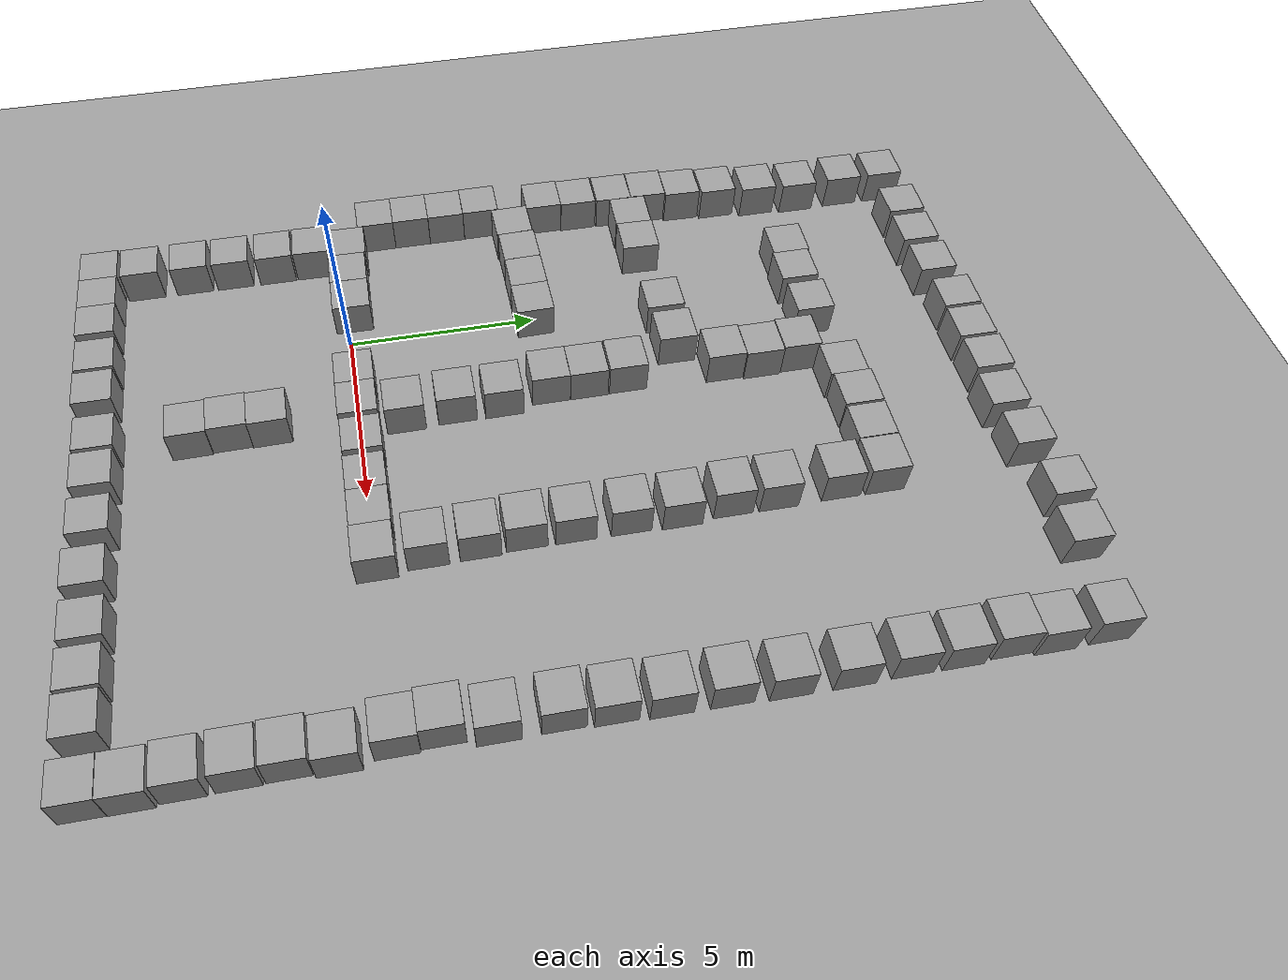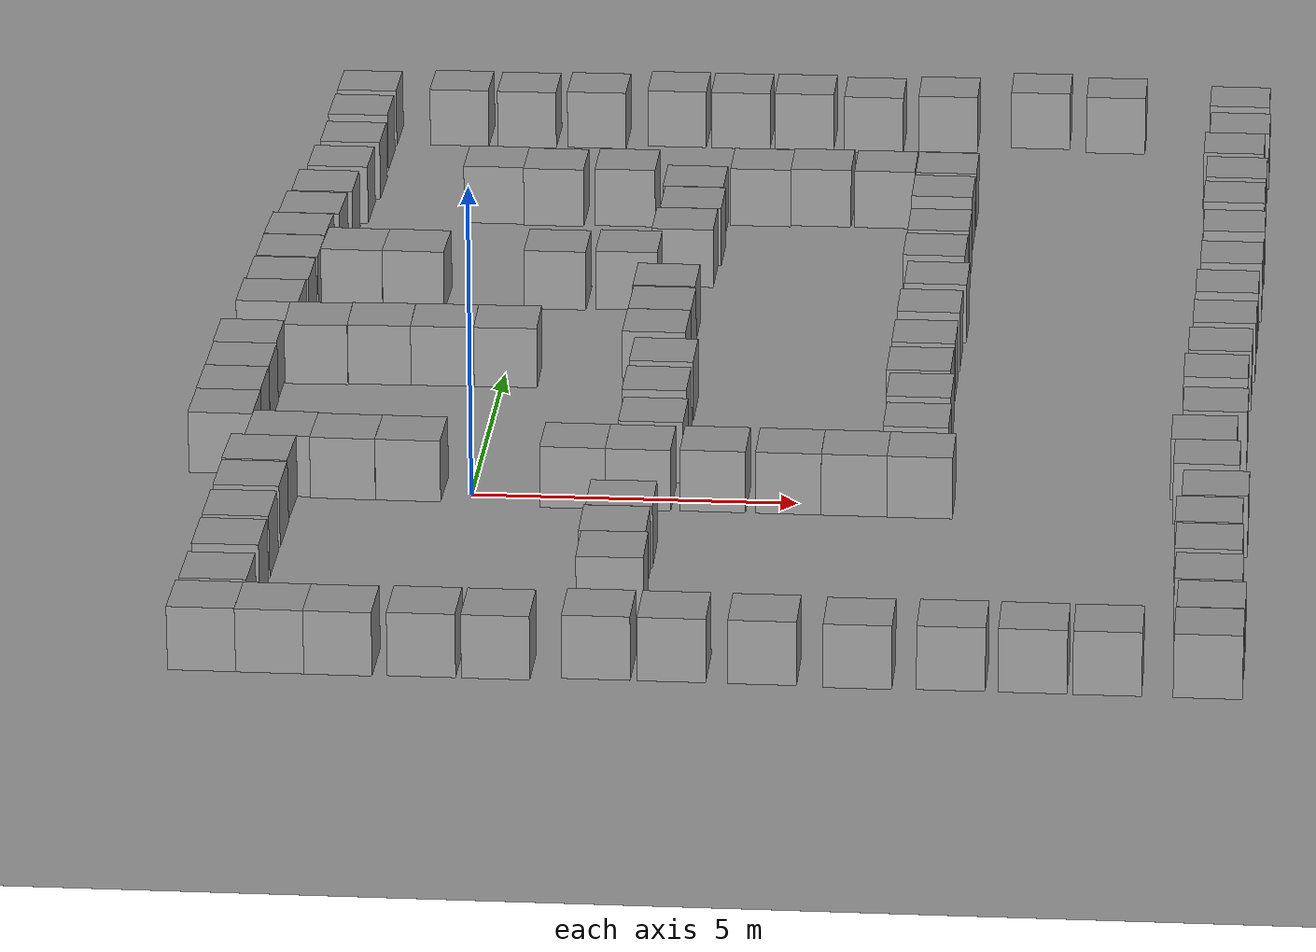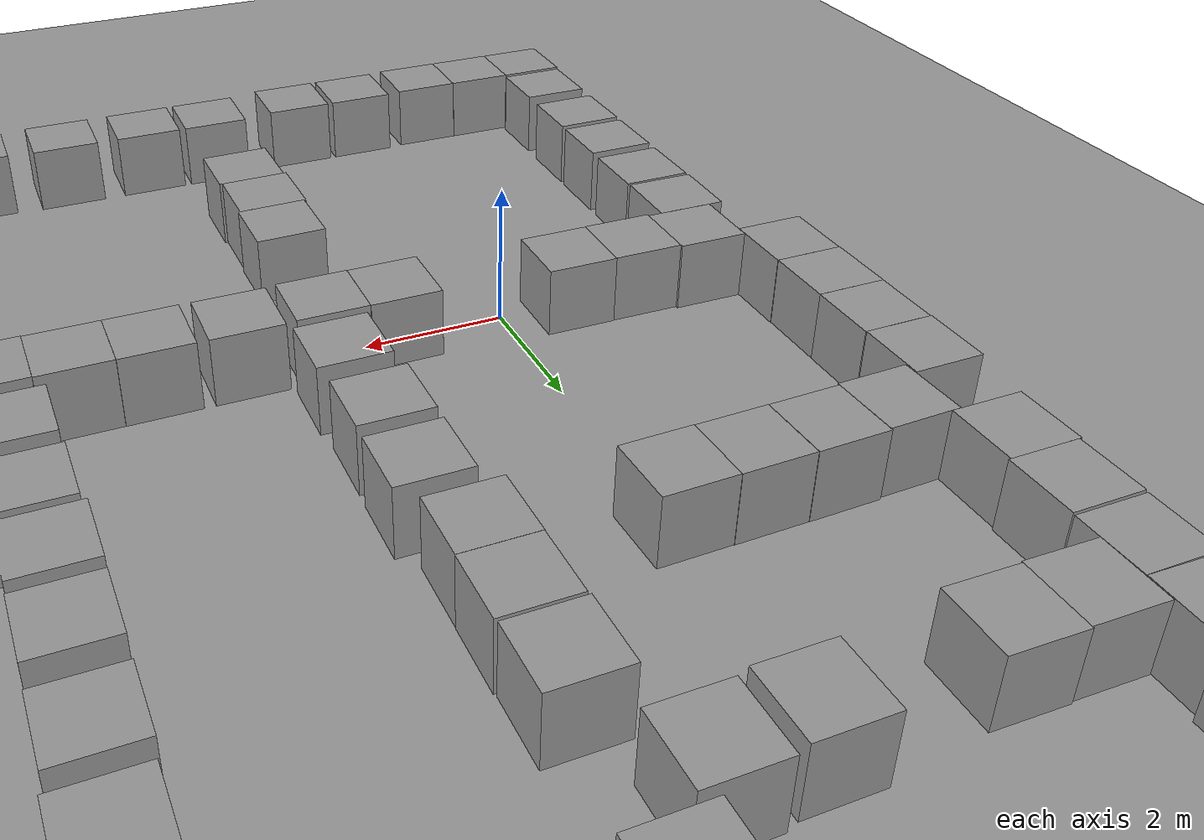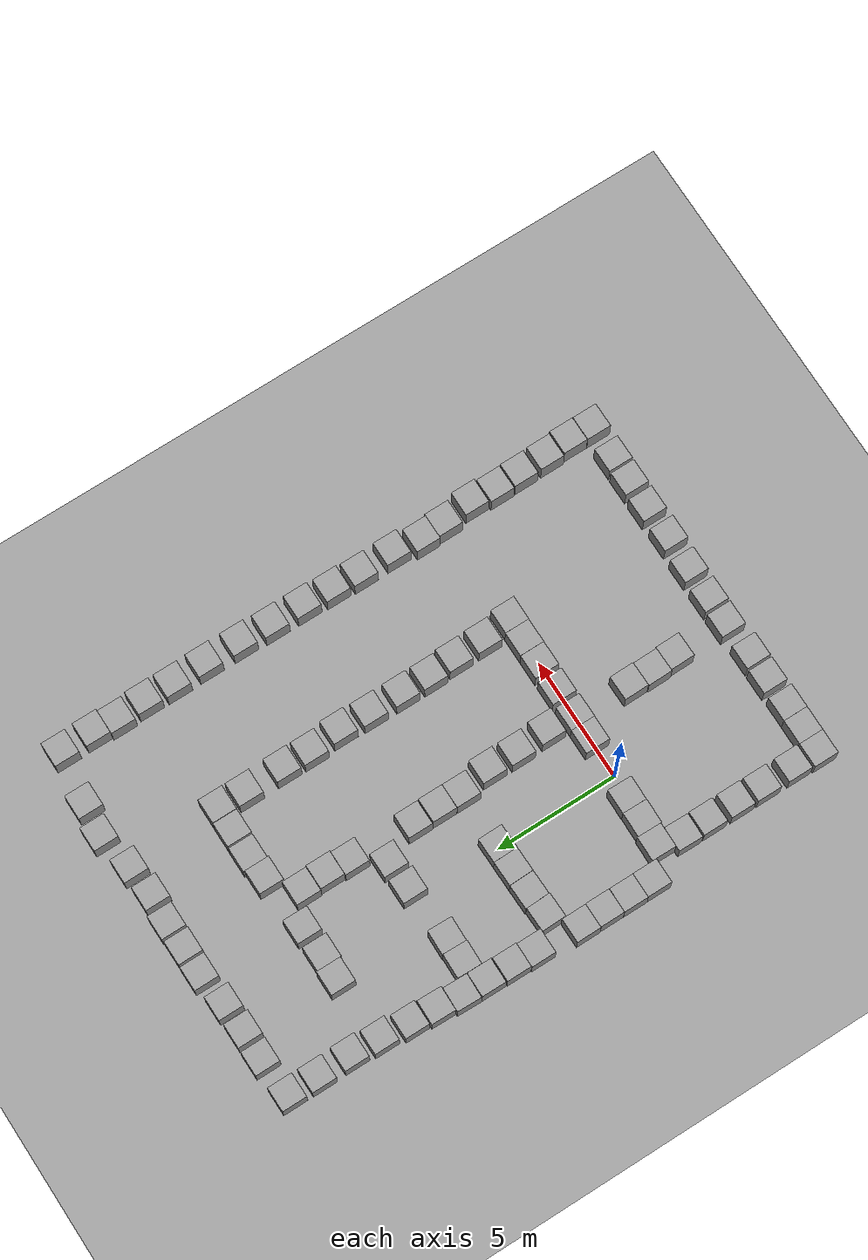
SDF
<sdf version="1.6">
 <world name="default">
  <light name="sun" type="directional">
   <pose>0 0 10 0 -0 0</pose>
   <diffuse>0.8 0.8 0.8 1</diffuse>
   <specular>0.2 0.2 0.2 1</specular>
   <attenuation>
    <range>1000</range>
    <constant>0.9</constant>
    <linear>0.01</linear>
    <quadratic>0.001</quadratic>
   </attenuation>
   <direction>0.5 0.1 -0.9</direction>
  </light>
  <scene><ambient>0.4 0.4 0.4 1</ambient><background>0.7 0.7 0.7 1</background><shadows>1</shadows></scene>
  <physics name="default_physics" default="0" type="ode">
   <max_step_size>0.01</max_step_size>
   <real_time_factor>1</real_time_factor>
   <real_time_update_rate>100</real_time_update_rate>
  </physics>
  <model name="ground_plane_0">
   <static>1</static>
   <link name="link">
    <collision name="collision">
     <geometry><plane><normal>0 0 1</normal><size>100 100</size></plane></geometry>
     <surface><friction><ode><mu>100</mu><mu2>50</mu2></ode></friction></surface>
    </collision>
    <visual name="visual">
     <cast_shadows>0</cast_shadows>
     <geometry><plane><normal>0 0 1</normal><size>100 100</size></plane></geometry>
     <material>
      <script><uri>file://media/materials/scripts/gazebo.material</uri><name>Gazebo/Grey</name></script>
     </material>
    </visual>
    <velocity_decay><linear>0</linear><angular>0</angular></velocity_decay>
   </link>
   <pose>0.497681 0 0 0 -0 0</pose>
  </model>
  <gravity>0 0 -9.8</gravity>
  <magnetic_field>6e-06 2.3e-05 -4.2e-05</magnetic_field>
  <atmosphere type="adiabatic"/>
  <spherical_coordinates>
   <surface_model>EARTH_WGS84</surface_model>
   <latitude_deg>0</latitude_deg>
   <longitude_deg>0</longitude_deg>
   <elevation>0</elevation>
   <heading_deg>0</heading_deg>
  </spherical_coordinates>
  <model name="unit_box_0_11">
   <pose>-0.949566 0.164537 0.49907 0.0001 -0 -0.010168</pose>
   <link name="link">
    <inertial>
     <mass>1</mass>
     <inertia>
      <ixx>0.166667</ixx>
      <ixy>0</ixy>
      <ixz>0</ixz>
      <iyy>0.166667</iyy>
      <iyz>0</iyz>
      <izz>0.166667</izz>
     </inertia>
    </inertial>
    <collision name="collision"><geometry><box><size>1 1 1</size></box></geometry></collision>
    <visual name="visual">
     <geometry><box><size>1 1 1</size></box></geometry>
     <material>
      <script><name>Gazebo/Grey</name><uri>file://media/materials/scripts/gazebo.material</uri></script>
     </material>
    </visual>
   </link>
  </model>
  <model name="unit_box_0_12">
   <pose>-1.95101 0.170149 0.49967 0.00066 -0 -0.013047</pose>
   <link name="link">
    <inertial>
     <mass>1</mass>
     <inertia>
      <ixx>0.166667</ixx>
      <ixy>0</ixy>
      <ixz>0</ixz>
      <iyy>0.166667</iyy>
      <iyz>0</iyz>
      <izz>0.166667</izz>
     </inertia>
    </inertial>
    <collision name="collision"><geometry><box><size>1 1 1</size></box></geometry></collision>
    <visual name="visual">
     <geometry><box><size>1 1 1</size></box></geometry>
     <material>
      <script><name>Gazebo/Grey</name><uri>file://media/materials/scripts/gazebo.material</uri></script>
     </material>
    </visual>
   </link>
  </model>
  <model name="unit_box_0_13">
   <pose>-2.95058 0.223115 0.49967 0.00066 0 -0.013393</pose>
   <link name="link">
    <inertial>
     <mass>1</mass>
     <inertia>
      <ixx>0.166667</ixx>
      <ixy>0</ixy>
      <ixz>0</ixz>
      <iyy>0.166667</iyy>
      <iyz>0</iyz>
      <izz>0.166667</izz>
     </inertia>
    </inertial>
    <collision name="collision"><geometry><box><size>1 1 1</size></box></geometry></collision>
    <visual name="visual">
     <geometry><box><size>1 1 1</size></box></geometry>
     <material>
      <script><name>Gazebo/Grey</name><uri>file://media/materials/scripts/gazebo.material</uri></script>
     </material>
    </visual>
   </link>
  </model>
  <model name="unit_box_0_14">
   <pose>-3.95128 1.06905 0.5 0 0 -0.002373</pose>
   <link name="link">
    <inertial>
     <mass>1</mass>
     <inertia>
      <ixx>0.166667</ixx>
      <ixy>0</ixy>
      <ixz>0</ixz>
      <iyy>0.166667</iyy>
      <iyz>0</iyz>
      <izz>0.166667</izz>
     </inertia>
    </inertial>
    <collision name="collision"><geometry><box><size>1 1 1</size></box></geometry></collision>
    <visual name="visual">
     <geometry><box><size>1 1 1</size></box></geometry>
     <material>
      <script><name>Gazebo/Grey</name><uri>file://media/materials/scripts/gazebo.material</uri></script>
     </material>
    </visual>
   </link>
  </model>
  <model name="unit_box_0_15">
   <pose>-3.95717 2.06918 0.49967 0 0.00066 -0.002203</pose>
   <link name="link">
    <inertial>
     <mass>1</mass>
     <inertia>
      <ixx>0.166667</ixx>
      <ixy>0</ixy>
      <ixz>0</ixz>
      <iyy>0.166667</iyy>
      <iyz>0</iyz>
      <izz>0.166667</izz>
     </inertia>
    </inertial>
    <collision name="collision"><geometry><box><size>1 1 1</size></box></geometry></collision>
    <visual name="visual">
     <geometry><box><size>1 1 1</size></box></geometry>
     <material>
      <script><name>Gazebo/Grey</name><uri>file://media/materials/scripts/gazebo.material</uri></script>
     </material>
    </visual>
   </link>
  </model>
  <model name="unit_box_0_16">
   <pose>-3.9524 3.07047 0.5 0 -0 0.000203</pose>
   <link name="link">
    <inertial>
     <mass>1</mass>
     <inertia>
      <ixx>0.166667</ixx>
      <ixy>0</ixy>
      <ixz>0</ixz>
      <iyy>0.166667</iyy>
      <iyz>0</iyz>
      <izz>0.166667</izz>
     </inertia>
    </inertial>
    <collision name="collision"><geometry><box><size>1 1 1</size></box></geometry></collision>
    <visual name="visual">
     <geometry><box><size>1 1 1</size></box></geometry>
     <material>
      <script><name>Gazebo/Grey</name><uri>file://media/materials/scripts/gazebo.material</uri></script>
     </material>
    </visual>
   </link>
  </model>
  <model name="unit_box_0_17">
   <pose>-3.96756 4.07164 0.49967 0 0.00066 0.002599</pose>
   <link name="link">
    <inertial>
     <mass>1</mass>
     <inertia>
      <ixx>0.166667</ixx>
      <ixy>0</ixy>
      <ixz>0</ixz>
      <iyy>0.166667</iyy>
      <iyz>0</iyz>
      <izz>0.166667</izz>
     </inertia>
    </inertial>
    <collision name="collision"><geometry><box><size>1 1 1</size></box></geometry></collision>
    <visual name="visual">
     <geometry><box><size>1 1 1</size></box></geometry>
     <material>
      <script><name>Gazebo/Grey</name><uri>file://media/materials/scripts/gazebo.material</uri></script>
     </material>
    </visual>
   </link>
  </model>
  <model name="unit_box_0_18">
   <pose>-2.96141 4.90048 0.49967 0.00066 -0 0.026859</pose>
   <link name="link">
    <inertial>
     <mass>1</mass>
     <inertia>
      <ixx>0.166667</ixx>
      <ixy>0</ixy>
      <ixz>0</ixz>
      <iyy>0.166667</iyy>
      <iyz>0</iyz>
      <izz>0.166667</izz>
     </inertia>
    </inertial>
    <collision name="collision"><geometry><box><size>1 1 1</size></box></geometry></collision>
    <visual name="visual">
     <geometry><box><size>1 1 1</size></box></geometry>
     <material>
      <script><name>Gazebo/Grey</name><uri>file://media/materials/scripts/gazebo.material</uri></script>
     </material>
    </visual>
   </link>
  </model>
  <model name="unit_box_0_19">
   <pose>-1.96159 4.95479 0.49907 -0.0001 -0 0.025121</pose>
   <link name="link">
    <inertial>
     <mass>1</mass>
     <inertia>
      <ixx>0.166667</ixx>
      <ixy>0</ixy>
      <ixz>0</ixz>
      <iyy>0.166667</iyy>
      <iyz>0</iyz>
      <izz>0.166667</izz>
     </inertia>
    </inertial>
    <collision name="collision"><geometry><box><size>1 1 1</size></box></geometry></collision>
    <visual name="visual">
     <geometry><box><size>1 1 1</size></box></geometry>
     <material>
      <script><name>Gazebo/Grey</name><uri>file://media/materials/scripts/gazebo.material</uri></script>
     </material>
    </visual>
   </link>
  </model>
  <model name="unit_box_0_20">
   <pose>-0.959822 4.97444 0.49907 -0.0001 -0 0.021531</pose>
   <link name="link">
    <inertial>
     <mass>1</mass>
     <inertia>
      <ixx>0.166667</ixx>
      <ixy>0</ixy>
      <ixz>0</ixz>
      <iyy>0.166667</iyy>
      <iyz>0</iyz>
      <izz>0.166667</izz>
     </inertia>
    </inertial>
    <collision name="collision"><geometry><box><size>1 1 1</size></box></geometry></collision>
    <visual name="visual">
     <geometry><box><size>1 1 1</size></box></geometry>
     <material>
      <script><name>Gazebo/Grey</name><uri>file://media/materials/scripts/gazebo.material</uri></script>
     </material>
    </visual>
   </link>
  </model>
  <model name="unit_box_0_23">
   <pose>0.040569 4.9896 0.49967 -0.00066 -0 0.020714</pose>
   <link name="link">
    <inertial>
     <mass>1</mass>
     <inertia>
      <ixx>0.166667</ixx>
      <ixy>0</ixy>
      <ixz>0</ixz>
      <iyy>0.166667</iyy>
      <iyz>0</iyz>
      <izz>0.166667</izz>
     </inertia>
    </inertial>
    <collision name="collision"><geometry><box><size>1 1 1</size></box></geometry></collision>
    <visual name="visual">
     <geometry><box><size>1 1 1</size></box></geometry>
     <material>
      <script><name>Gazebo/Grey</name><uri>file://media/materials/scripts/gazebo.material</uri></script>
     </material>
    </visual>
   </link>
  </model>
  <model name="unit_box_0_30">
   <pose>0.500605 8.46428 0.499798 0.000404 1e-06 0</pose>
   <link name="link">
    <inertial>
     <mass>1</mass>
     <inertia>
      <ixx>0.166667</ixx>
      <ixy>0</ixy>
      <ixz>0</ixz>
      <iyy>0.166667</iyy>
      <iyz>0</iyz>
      <izz>0.166667</izz>
     </inertia>
    </inertial>
    <collision name="collision"><geometry><box><size>1 1 1</size></box></geometry></collision>
    <visual name="visual">
     <geometry><box><size>1 1 1</size></box></geometry>
     <material>
      <script><name>Gazebo/Grey</name><uri>file://media/materials/scripts/gazebo.material</uri></script>
     </material>
    </visual>
   </link>
  </model>
  <model name="unit_box_0_33">
   <pose>-3.48262 12.1839 0.499798 -0.000404 1e-06 1e-06</pose>
   <link name="link">
    <inertial>
     <mass>1</mass>
     <inertia>
      <ixx>0.166667</ixx>
      <ixy>0</ixy>
      <ixz>0</ixz>
      <iyy>0.166667</iyy>
      <iyz>0</iyz>
      <izz>0.166667</izz>
     </inertia>
    </inertial>
    <collision name="collision"><geometry><box><size>1 1 1</size></box></geometry></collision>
    <visual name="visual">
     <geometry><box><size>1 1 1</size></box></geometry>
     <material>
      <script><name>Gazebo/Grey</name><uri>file://media/materials/scripts/gazebo.material</uri></script>
     </material>
    </visual>
   </link>
  </model>
  <model name="unit_box_0_34">
   <pose>-3.84483 5.89053 0.49967 0 0.00066 0.000679</pose>
   <link name="link">
    <inertial>
     <mass>1</mass>
     <inertia>
      <ixx>0.166667</ixx>
      <ixy>0</ixy>
      <ixz>0</ixz>
      <iyy>0.166667</iyy>
      <iyz>0</iyz>
      <izz>0.166667</izz>
     </inertia>
    </inertial>
    <collision name="collision"><geometry><box><size>1 1 1</size></box></geometry></collision>
    <visual name="visual">
     <geometry><box><size>1 1 1</size></box></geometry>
     <material>
      <script><name>Gazebo/Grey</name><uri>file://media/materials/scripts/gazebo.material</uri></script>
     </material>
    </visual>
   </link>
  </model>
  <model name="unit_box_0_34_clone">
   <pose>-3.80881 6.89097 0.5 0 -0 9.8e-05</pose>
   <link name="link">
    <inertial>
     <mass>1</mass>
     <inertia>
      <ixx>0.166667</ixx>
      <ixy>0</ixy>
      <ixz>0</ixz>
      <iyy>0.166667</iyy>
      <iyz>0</iyz>
      <izz>0.166667</izz>
     </inertia>
    </inertial>
    <collision name="collision"><geometry><box><size>1 1 1</size></box></geometry></collision>
    <visual name="visual">
     <geometry><box><size>1 1 1</size></box></geometry>
     <material>
      <script><name>Gazebo/Grey</name><uri>file://media/materials/scripts/gazebo.material</uri></script>
     </material>
    </visual>
   </link>
  </model>
  <model name="unit_box_0_34_clone_0">
   <pose>-3.78755 7.93029 0.499798 0.000404 0 -0.003906</pose>
   <link name="link">
    <inertial>
     <mass>1</mass>
     <inertia>
      <ixx>0.166667</ixx>
      <ixy>0</ixy>
      <ixz>0</ixz>
      <iyy>0.166667</iyy>
      <iyz>0</iyz>
      <izz>0.166667</izz>
     </inertia>
    </inertial>
    <collision name="collision"><geometry><box><size>1 1 1</size></box></geometry></collision>
    <visual name="visual">
     <geometry><box><size>1 1 1</size></box></geometry>
     <material>
      <script><name>Gazebo/Grey</name><uri>file://media/materials/scripts/gazebo.material</uri></script>
     </material>
    </visual>
   </link>
  </model>
  <model name="unit_box_0_34_clone_1">
   <pose>-2.77833 8.29419 0.49967 0.00066 -0 -0.018577</pose>
   <link name="link">
    <inertial>
     <mass>1</mass>
     <inertia>
      <ixx>0.166667</ixx>
      <ixy>0</ixy>
      <ixz>0</ixz>
      <iyy>0.166667</iyy>
      <iyz>0</iyz>
      <izz>0.166667</izz>
     </inertia>
    </inertial>
    <collision name="collision"><geometry><box><size>1 1 1</size></box></geometry></collision>
    <visual name="visual">
     <geometry><box><size>1 1 1</size></box></geometry>
     <material>
      <script><name>Gazebo/Grey</name><uri>file://media/materials/scripts/gazebo.material</uri></script>
     </material>
    </visual>
   </link>
  </model>
  <model name="unit_box_0_34_clone_0_clone">
   <pose>-3.77888 8.94276 0.49912 0 0 -0.025372</pose>
   <link name="link">
    <inertial>
     <mass>1</mass>
     <inertia>
      <ixx>0.166667</ixx>
      <ixy>0</ixy>
      <ixz>0</ixz>
      <iyy>0.166667</iyy>
      <iyz>0</iyz>
      <izz>0.166667</izz>
     </inertia>
    </inertial>
    <collision name="collision"><geometry><box><size>1 1 1</size></box></geometry></collision>
    <visual name="visual">
     <geometry><box><size>1 1 1</size></box></geometry>
     <material>
      <script><name>Gazebo/Grey</name><uri>file://media/materials/scripts/gazebo.material</uri></script>
     </material>
    </visual>
   </link>
  </model>
  <model name="unit_box_0_34_clone_0_clone_0">
   <pose>-3.67164 9.94701 0.49967 -0.00066 -0 -0.016817</pose>
   <link name="link">
    <inertial>
     <mass>1</mass>
     <inertia>
      <ixx>0.166667</ixx>
      <ixy>0</ixy>
      <ixz>0</ixz>
      <iyy>0.166667</iyy>
      <iyz>0</iyz>
      <izz>0.166667</izz>
     </inertia>
    </inertial>
    <collision name="collision"><geometry><box><size>1 1 1</size></box></geometry></collision>
    <visual name="visual">
     <geometry><box><size>1 1 1</size></box></geometry>
     <material>
      <script><name>Gazebo/Grey</name><uri>file://media/materials/scripts/gazebo.material</uri></script>
     </material>
    </visual>
   </link>
  </model>
  <model name="unit_box_0_34_clone_0_clone_1">
   <pose>-3.59427 10.9907 0.499798 -0.000404 -1e-06 1e-06</pose>
   <link name="link">
    <inertial>
     <mass>1</mass>
     <inertia>
      <ixx>0.166667</ixx>
      <ixy>0</ixy>
      <ixz>0</ixz>
      <iyy>0.166667</iyy>
      <iyz>0</iyz>
      <izz>0.166667</izz>
     </inertia>
    </inertial>
    <collision name="collision"><geometry><box><size>1 1 1</size></box></geometry></collision>
    <visual name="visual">
     <geometry><box><size>1 1 1</size></box></geometry>
     <material>
      <script><name>Gazebo/Grey</name><uri>file://media/materials/scripts/gazebo.material</uri></script>
     </material>
    </visual>
   </link>
  </model>
  <model name="unit_box_0_34_clone_0_clone_3">
   <pose>1.65614 8.52704 0.499798 -0.000404 1e-06 1e-06</pose>
   <link name="link">
    <inertial>
     <mass>1</mass>
     <inertia>
      <ixx>0.166667</ixx>
      <ixy>0</ixy>
      <ixz>0</ixz>
      <iyy>0.166667</iyy>
      <iyz>0</iyz>
      <izz>0.166667</izz>
     </inertia>
    </inertial>
    <collision name="collision"><geometry><box><size>1 1 1</size></box></geometry></collision>
    <visual name="visual">
     <geometry><box><size>1 1 1</size></box></geometry>
     <material>
      <script><name>Gazebo/Grey</name><uri>file://media/materials/scripts/gazebo.material</uri></script>
     </material>
    </visual>
   </link>
  </model>
  <model name="unit_box_0_34_clone_0_clone_4">
   <pose>2.40454 4.99714 0.499798 0.000404 -0 -0.000155</pose>
   <link name="link">
    <inertial>
     <mass>1</mass>
     <inertia>
      <ixx>0.166667</ixx>
      <ixy>0</ixy>
      <ixz>0</ixz>
      <iyy>0.166667</iyy>
      <iyz>0</iyz>
      <izz>0.166667</izz>
     </inertia>
    </inertial>
    <collision name="collision"><geometry><box><size>1 1 1</size></box></geometry></collision>
    <visual name="visual">
     <geometry><box><size>1 1 1</size></box></geometry>
     <material>
      <script><name>Gazebo/Grey</name><uri>file://media/materials/scripts/gazebo.material</uri></script>
     </material>
    </visual>
   </link>
  </model>
  <model name="unit_box_0_34_clone_0_clone_5">
   <pose>2.41027 5.99947 0.499798 0.000404 1e-06 -0.001291</pose>
   <link name="link">
    <inertial>
     <mass>1</mass>
     <inertia>
      <ixx>0.166667</ixx>
      <ixy>0</ixy>
      <ixz>0</ixz>
      <iyy>0.166667</iyy>
      <iyz>0</iyz>
      <izz>0.166667</izz>
     </inertia>
    </inertial>
    <collision name="collision"><geometry><box><size>1 1 1</size></box></geometry></collision>
    <visual name="visual">
     <geometry><box><size>1 1 1</size></box></geometry>
     <material>
      <script><name>Gazebo/Grey</name><uri>file://media/materials/scripts/gazebo.material</uri></script>
     </material>
    </visual>
   </link>
  </model>
  <model name="unit_box_0_34_clone_0_clone_6">
   <pose>2.39059 7.04162 0.499798 -0.000404 1e-06 1e-06</pose>
   <link name="link">
    <inertial>
     <mass>1</mass>
     <inertia>
      <ixx>0.166667</ixx>
      <ixy>0</ixy>
      <ixz>0</ixz>
      <iyy>0.166667</iyy>
      <iyz>0</iyz>
      <izz>0.166667</izz>
     </inertia>
    </inertial>
    <collision name="collision"><geometry><box><size>1 1 1</size></box></geometry></collision>
    <visual name="visual">
     <geometry><box><size>1 1 1</size></box></geometry>
     <material>
      <script><name>Gazebo/Grey</name><uri>file://media/materials/scripts/gazebo.material</uri></script>
     </material>
    </visual>
   </link>
  </model>
  <model name="unit_box_0_34_clone_0_clone_7">
   <pose>2.47381 9.63829 0.49907 0 -0.0001 -0.000459</pose>
   <link name="link">
    <inertial>
     <mass>1</mass>
     <inertia>
      <ixx>0.166667</ixx>
      <ixy>0</ixy>
      <ixz>0</ixz>
      <iyy>0.166667</iyy>
      <iyz>0</iyz>
      <izz>0.166667</izz>
     </inertia>
    </inertial>
    <collision name="collision"><geometry><box><size>1 1 1</size></box></geometry></collision>
    <visual name="visual">
     <geometry><box><size>1 1 1</size></box></geometry>
     <material>
      <script><name>Gazebo/Grey</name><uri>file://media/materials/scripts/gazebo.material</uri></script>
     </material>
    </visual>
   </link>
  </model>
  <model name="unit_box_0_34_clone_0_clone_8">
   <pose>2.52689 10.6415 0.499798 -0.000404 0 -0.000669</pose>
   <link name="link">
    <inertial>
     <mass>1</mass>
     <inertia>
      <ixx>0.166667</ixx>
      <ixy>0</ixy>
      <ixz>0</ixz>
      <iyy>0.166667</iyy>
      <iyz>0</iyz>
      <izz>0.166667</izz>
     </inertia>
    </inertial>
    <collision name="collision"><geometry><box><size>1 1 1</size></box></geometry></collision>
    <visual name="visual">
     <geometry><box><size>1 1 1</size></box></geometry>
     <material>
      <script><name>Gazebo/Grey</name><uri>file://media/materials/scripts/gazebo.material</uri></script>
     </material>
    </visual>
   </link>
  </model>
  <model name="unit_box_0_34_clone_0_clone_9">
   <pose>2.48371 11.6566 0.499798 -0.000404 1e-06 1e-06</pose>
   <link name="link">
    <inertial>
     <mass>1</mass>
     <inertia>
      <ixx>0.166667</ixx>
      <ixy>0</ixy>
      <ixz>0</ixz>
      <iyy>0.166667</iyy>
      <iyz>0</iyz>
      <izz>0.166667</izz>
     </inertia>
    </inertial>
    <collision name="collision"><geometry><box><size>1 1 1</size></box></geometry></collision>
    <visual name="visual">
     <geometry><box><size>1 1 1</size></box></geometry>
     <material>
      <script><name>Gazebo/Grey</name><uri>file://media/materials/scripts/gazebo.material</uri></script>
     </material>
    </visual>
   </link>
  </model>
  <model name="unit_box_0_34_clone_0_clone_10">
   <pose>0.106327 12.3129 0.499798 0.000404 1e-06 1e-05</pose>
   <link name="link">
    <inertial>
     <mass>1</mass>
     <inertia>
      <ixx>0.166667</ixx>
      <ixy>0</ixy>
      <ixz>0</ixz>
      <iyy>0.166667</iyy>
      <iyz>0</iyz>
      <izz>0.166667</izz>
     </inertia>
    </inertial>
    <collision name="collision"><geometry><box><size>1 1 1</size></box></geometry></collision>
    <visual name="visual">
     <geometry><box><size>1 1 1</size></box></geometry>
     <material>
      <script><name>Gazebo/Grey</name><uri>file://media/materials/scripts/gazebo.material</uri></script>
     </material>
    </visual>
   </link>
  </model>
  <model name="unit_box_0_34_clone_0_clone_11">
   <pose>1.29109 12.3791 0.499798 0.000404 1e-06 5e-06</pose>
   <link name="link">
    <inertial>
     <mass>1</mass>
     <inertia>
      <ixx>0.166667</ixx>
      <ixy>0</ixy>
      <ixz>0</ixz>
      <iyy>0.166667</iyy>
      <iyz>0</iyz>
      <izz>0.166667</izz>
     </inertia>
    </inertial>
    <collision name="collision"><geometry><box><size>1 1 1</size></box></geometry></collision>
    <visual name="visual">
     <geometry><box><size>1 1 1</size></box></geometry>
     <material>
      <script><name>Gazebo/Grey</name><uri>file://media/materials/scripts/gazebo.material</uri></script>
     </material>
    </visual>
   </link>
  </model>
  <model name="unit_box_0_33_clone">
   <pose>-0.89374 12.353 0.499798 0.000404 1e-06 0</pose>
   <link name="link">
    <inertial>
     <mass>1</mass>
     <inertia>
      <ixx>0.166667</ixx>
      <ixy>0</ixy>
      <ixz>0</ixz>
      <iyy>0.166667</iyy>
      <iyz>0</iyz>
      <izz>0.166667</izz>
     </inertia>
    </inertial>
    <collision name="collision"><geometry><box><size>1 1 1</size></box></geometry></collision>
    <visual name="visual">
     <geometry><box><size>1 1 1</size></box></geometry>
     <material>
      <script><name>Gazebo/Grey</name><uri>file://media/materials/scripts/gazebo.material</uri></script>
     </material>
    </visual>
   </link>
  </model>
  <model name="unit_box_0_34_clone_0_clone_11_clone">
   <pose>3.53343 12.5549 0.499798 -0.000404 1e-06 0.000489</pose>
   <link name="link">
    <inertial>
     <mass>1</mass>
     <inertia>
      <ixx>0.166667</ixx>
      <ixy>0</ixy>
      <ixz>0</ixz>
      <iyy>0.166667</iyy>
      <iyz>0</iyz>
      <izz>0.166667</izz>
     </inertia>
    </inertial>
    <collision name="collision"><geometry><box><size>1 1 1</size></box></geometry></collision>
    <visual name="visual">
     <geometry><box><size>1 1 1</size></box></geometry>
     <material>
      <script><name>Gazebo/Grey</name><uri>file://media/materials/scripts/gazebo.material</uri></script>
     </material>
    </visual>
   </link>
  </model>
  <model name="unit_box_0_34_clone_0_clone_11_clone_0">
   <pose>4.53348 12.6157 0.499798 0.000404 -0 0.000402</pose>
   <link name="link">
    <inertial>
     <mass>1</mass>
     <inertia>
      <ixx>0.166667</ixx>
      <ixy>0</ixy>
      <ixz>0</ixz>
      <iyy>0.166667</iyy>
      <iyz>0</iyz>
      <izz>0.166667</izz>
     </inertia>
    </inertial>
    <collision name="collision"><geometry><box><size>1 1 1</size></box></geometry></collision>
    <visual name="visual">
     <geometry><box><size>1 1 1</size></box></geometry>
     <material>
      <script><name>Gazebo/Grey</name><uri>file://media/materials/scripts/gazebo.material</uri></script>
     </material>
    </visual>
   </link>
  </model>
  <model name="unit_box_0_34_clone_0_clone_11_clone_1">
   <pose>5.59209 12.6088 0.499798 0.000404 1e-06 1e-06</pose>
   <link name="link">
    <inertial>
     <mass>1</mass>
     <inertia>
      <ixx>0.166667</ixx>
      <ixy>0</ixy>
      <ixz>0</ixz>
      <iyy>0.166667</iyy>
      <iyz>0</iyz>
      <izz>0.166667</izz>
     </inertia>
    </inertial>
    <collision name="collision"><geometry><box><size>1 1 1</size></box></geometry></collision>
    <visual name="visual">
     <geometry><box><size>1 1 1</size></box></geometry>
     <material>
      <script><name>Gazebo/Grey</name><uri>file://media/materials/scripts/gazebo.material</uri></script>
     </material>
    </visual>
   </link>
  </model>
  <model name="unit_box_0_34_clone_0_clone_11_clone_2">
   <pose>6.6091 12.6021 0.499798 0.000404 1e-06 1e-06</pose>
   <link name="link">
    <inertial>
     <mass>1</mass>
     <inertia>
      <ixx>0.166667</ixx>
      <ixy>0</ixy>
      <ixz>0</ixz>
      <iyy>0.166667</iyy>
      <iyz>0</iyz>
      <izz>0.166667</izz>
     </inertia>
    </inertial>
    <collision name="collision"><geometry><box><size>1 1 1</size></box></geometry></collision>
    <visual name="visual">
     <geometry><box><size>1 1 1</size></box></geometry>
     <material>
      <script><name>Gazebo/Grey</name><uri>file://media/materials/scripts/gazebo.material</uri></script>
     </material>
    </visual>
   </link>
  </model>
  <model name="unit_box_0_34_clone_0_clone_11_clone_3">
   <pose>6.60251 11.4819 0.499798 0.000404 1e-06 1e-06</pose>
   <link name="link">
    <inertial>
     <mass>1</mass>
     <inertia>
      <ixx>0.166667</ixx>
      <ixy>0</ixy>
      <ixz>0</ixz>
      <iyy>0.166667</iyy>
      <iyz>0</iyz>
      <izz>0.166667</izz>
     </inertia>
    </inertial>
    <collision name="collision"><geometry><box><size>1 1 1</size></box></geometry></collision>
    <visual name="visual">
     <geometry><box><size>1 1 1</size></box></geometry>
     <material>
      <script><name>Gazebo/Grey</name><uri>file://media/materials/scripts/gazebo.material</uri></script>
     </material>
    </visual>
   </link>
  </model>
  <model name="unit_box_0_34_clone_0_clone_11_clone_4">
   <pose>6.62713 9.88718 0.499798 0.000404 1e-06 1e-06</pose>
   <link name="link">
    <inertial>
     <mass>1</mass>
     <inertia>
      <ixx>0.166667</ixx>
      <ixy>0</ixy>
      <ixz>0</ixz>
      <iyy>0.166667</iyy>
      <iyz>0</iyz>
      <izz>0.166667</izz>
     </inertia>
    </inertial>
    <collision name="collision"><geometry><box><size>1 1 1</size></box></geometry></collision>
    <visual name="visual">
     <geometry><box><size>1 1 1</size></box></geometry>
     <material>
      <script><name>Gazebo/Grey</name><uri>file://media/materials/scripts/gazebo.material</uri></script>
     </material>
    </visual>
   </link>
  </model>
  <model name="unit_box_0_34_clone_0_clone_11_clone_5">
   <pose>6.62038 8.73386 0.499798 0.000404 1e-06 1e-06</pose>
   <link name="link">
    <inertial>
     <mass>1</mass>
     <inertia>
      <ixx>0.166667</ixx>
      <ixy>0</ixy>
      <ixz>0</ixz>
      <iyy>0.166667</iyy>
      <iyz>0</iyz>
      <izz>0.166667</izz>
     </inertia>
    </inertial>
    <collision name="collision"><geometry><box><size>1 1 1</size></box></geometry></collision>
    <visual name="visual">
     <geometry><box><size>1 1 1</size></box></geometry>
     <material>
      <script><name>Gazebo/Grey</name><uri>file://media/materials/scripts/gazebo.material</uri></script>
     </material>
    </visual>
   </link>
  </model>
  <model name="unit_box_0_34_clone_0_clone_11_clone_6">
   <pose>6.71449 7.44455 0.499798 0.000404 1e-06 1e-06</pose>
   <link name="link">
    <inertial>
     <mass>1</mass>
     <inertia>
      <ixx>0.166667</ixx>
      <ixy>0</ixy>
      <ixz>0</ixz>
      <iyy>0.166667</iyy>
      <iyz>0</iyz>
      <izz>0.166667</izz>
     </inertia>
    </inertial>
    <collision name="collision"><geometry><box><size>1 1 1</size></box></geometry></collision>
    <visual name="visual">
     <geometry><box><size>1 1 1</size></box></geometry>
     <material>
      <script><name>Gazebo/Grey</name><uri>file://media/materials/scripts/gazebo.material</uri></script>
     </material>
    </visual>
   </link>
  </model>
  <model name="unit_box_0_34_clone_0_clone_11_clone_7">
   <pose>6.67328 6.19035 0.499798 0.000404 1e-06 1e-06</pose>
   <link name="link">
    <inertial>
     <mass>1</mass>
     <inertia>
      <ixx>0.166667</ixx>
      <ixy>0</ixy>
      <ixz>0</ixz>
      <iyy>0.166667</iyy>
      <iyz>0</iyz>
      <izz>0.166667</izz>
     </inertia>
    </inertial>
    <collision name="collision"><geometry><box><size>1 1 1</size></box></geometry></collision>
    <visual name="visual">
     <geometry><box><size>1 1 1</size></box></geometry>
     <material>
      <script><name>Gazebo/Grey</name><uri>file://media/materials/scripts/gazebo.material</uri></script>
     </material>
    </visual>
   </link>
  </model>
  <model name="unit_box_0_34_clone_0_clone_11_clone_8">
   <pose>6.66555 4.83451 0.499798 0.000404 1e-06 1e-06</pose>
   <link name="link">
    <inertial>
     <mass>1</mass>
     <inertia>
      <ixx>0.166667</ixx>
      <ixy>0</ixy>
      <ixz>0</ixz>
      <iyy>0.166667</iyy>
      <iyz>0</iyz>
      <izz>0.166667</izz>
     </inertia>
    </inertial>
    <collision name="collision"><geometry><box><size>1 1 1</size></box></geometry></collision>
    <visual name="visual">
     <geometry><box><size>1 1 1</size></box></geometry>
     <material>
      <script><name>Gazebo/Grey</name><uri>file://media/materials/scripts/gazebo.material</uri></script>
     </material>
    </visual>
   </link>
  </model>
  <model name="unit_box_0_34_clone_0_clone_11_clone_9">
   <pose>6.65852 3.64831 0.499798 0.000404 1e-06 1e-06</pose>
   <link name="link">
    <inertial>
     <mass>1</mass>
     <inertia>
      <ixx>0.166667</ixx>
      <ixy>0</ixy>
      <ixz>0</ixz>
      <iyy>0.166667</iyy>
      <iyz>0</iyz>
      <izz>0.166667</izz>
     </inertia>
    </inertial>
    <collision name="collision"><geometry><box><size>1 1 1</size></box></geometry></collision>
    <visual name="visual">
     <geometry><box><size>1 1 1</size></box></geometry>
     <material>
      <script><name>Gazebo/Grey</name><uri>file://media/materials/scripts/gazebo.material</uri></script>
     </material>
    </visual>
   </link>
  </model>
  <model name="unit_box_0_34_clone_0_clone_11_clone_10">
   <pose>6.71962 2.52993 0.499798 0.000404 1e-06 1e-06</pose>
   <link name="link">
    <inertial>
     <mass>1</mass>
     <inertia>
      <ixx>0.166667</ixx>
      <ixy>0</ixy>
      <ixz>0</ixz>
      <iyy>0.166667</iyy>
      <iyz>0</iyz>
      <izz>0.166667</izz>
     </inertia>
    </inertial>
    <collision name="collision"><geometry><box><size>1 1 1</size></box></geometry></collision>
    <visual name="visual">
     <geometry><box><size>1 1 1</size></box></geometry>
     <material>
      <script><name>Gazebo/Grey</name><uri>file://media/materials/scripts/gazebo.material</uri></script>
     </material>
    </visual>
   </link>
  </model>
  <model name="unit_box_0_34_clone_0_clone_11_clone_11">
   <pose>6.74618 1.27647 0.499798 0.000404 1e-06 1e-06</pose>
   <link name="link">
    <inertial>
     <mass>1</mass>
     <inertia>
      <ixx>0.166667</ixx>
      <ixy>0</ixy>
      <ixz>0</ixz>
      <iyy>0.166667</iyy>
      <iyz>0</iyz>
      <izz>0.166667</izz>
     </inertia>
    </inertial>
    <collision name="collision"><geometry><box><size>1 1 1</size></box></geometry></collision>
    <visual name="visual">
     <geometry><box><size>1 1 1</size></box></geometry>
     <material>
      <script><name>Gazebo/Grey</name><uri>file://media/materials/scripts/gazebo.material</uri></script>
     </material>
    </visual>
   </link>
  </model>
  <model name="unit_box_0_34_clone_0_clone_11_clone_12">
   <pose>6.87925 0.056343 0.499798 -0.000404 1e-06 0.002412</pose>
   <link name="link">
    <inertial>
     <mass>1</mass>
     <inertia>
      <ixx>0.166667</ixx>
      <ixy>0</ixy>
      <ixz>0</ixz>
      <iyy>0.166667</iyy>
      <iyz>0</iyz>
      <izz>0.166667</izz>
     </inertia>
    </inertial>
    <collision name="collision"><geometry><box><size>1 1 1</size></box></geometry></collision>
    <visual name="visual">
     <geometry><box><size>1 1 1</size></box></geometry>
     <material>
      <script><name>Gazebo/Grey</name><uri>file://media/materials/scripts/gazebo.material</uri></script>
     </material>
    </visual>
   </link>
  </model>
  <model name="unit_box_0_34_clone_0_clone_11_clone_13">
   <pose>5.87884 0.066433 0.499798 0.000404 -0 0.003125</pose>
   <link name="link">
    <inertial>
     <mass>1</mass>
     <inertia>
      <ixx>0.166667</ixx>
      <ixy>0</ixy>
      <ixz>0</ixz>
      <iyy>0.166667</iyy>
      <iyz>0</iyz>
      <izz>0.166667</izz>
     </inertia>
    </inertial>
    <collision name="collision"><geometry><box><size>1 1 1</size></box></geometry></collision>
    <visual name="visual">
     <geometry><box><size>1 1 1</size></box></geometry>
     <material>
      <script><name>Gazebo/Grey</name><uri>file://media/materials/scripts/gazebo.material</uri></script>
     </material>
    </visual>
   </link>
  </model>
  <model name="unit_box_0_34_clone_0_clone_11_clone_14">
   <pose>4.87804 0.067524 0.499798 -0.000404 0 0.003949</pose>
   <link name="link">
    <inertial>
     <mass>1</mass>
     <inertia>
      <ixx>0.166667</ixx>
      <ixy>0</ixy>
      <ixz>0</ixz>
      <iyy>0.166667</iyy>
      <iyz>0</iyz>
      <izz>0.166667</izz>
     </inertia>
    </inertial>
    <collision name="collision"><geometry><box><size>1 1 1</size></box></geometry></collision>
    <visual name="visual">
     <geometry><box><size>1 1 1</size></box></geometry>
     <material>
      <script><name>Gazebo/Grey</name><uri>file://media/materials/scripts/gazebo.material</uri></script>
     </material>
    </visual>
   </link>
  </model>
  <model name="unit_box_0_34_clone_0_clone_11_clone_15">
   <pose>3.72473 0.072234 0.499798 0.000404 1e-06 2e-06</pose>
   <link name="link">
    <inertial>
     <mass>1</mass>
     <inertia>
      <ixx>0.166667</ixx>
      <ixy>0</ixy>
      <ixz>0</ixz>
      <iyy>0.166667</iyy>
      <iyz>0</iyz>
      <izz>0.166667</izz>
     </inertia>
    </inertial>
    <collision name="collision"><geometry><box><size>1 1 1</size></box></geometry></collision>
    <visual name="visual">
     <geometry><box><size>1 1 1</size></box></geometry>
     <material>
      <script><name>Gazebo/Grey</name><uri>file://media/materials/scripts/gazebo.material</uri></script>
     </material>
    </visual>
   </link>
  </model>
  <model name="unit_box_0_34_clone_0_clone_11_clone_16">
   <pose>2.58278 0.044371 0.49907 -0.0001 -0 0.000192</pose>
   <link name="link">
    <inertial>
     <mass>1</mass>
     <inertia>
      <ixx>0.166667</ixx>
      <ixy>0</ixy>
      <ixz>0</ixz>
      <iyy>0.166667</iyy>
      <iyz>0</iyz>
      <izz>0.166667</izz>
     </inertia>
    </inertial>
    <collision name="collision"><geometry><box><size>1 1 1</size></box></geometry></collision>
    <visual name="visual">
     <geometry><box><size>1 1 1</size></box></geometry>
     <material>
      <script><name>Gazebo/Grey</name><uri>file://media/materials/scripts/gazebo.material</uri></script>
     </material>
    </visual>
   </link>
  </model>
  <model name="unit_box_0_34_clone_0_clone_11_clone_17">
   <pose>2.68039 1.19555 0.499798 0.000404 1e-06 2e-06</pose>
   <link name="link">
    <inertial>
     <mass>1</mass>
     <inertia>
      <ixx>0.166667</ixx>
      <ixy>0</ixy>
      <ixz>0</ixz>
      <iyy>0.166667</iyy>
      <iyz>0</iyz>
      <izz>0.166667</izz>
     </inertia>
    </inertial>
    <collision name="collision"><geometry><box><size>1 1 1</size></box></geometry></collision>
    <visual name="visual">
     <geometry><box><size>1 1 1</size></box></geometry>
     <material>
      <script><name>Gazebo/Grey</name><uri>file://media/materials/scripts/gazebo.material</uri></script>
     </material>
    </visual>
   </link>
  </model>
  <model name="unit_box_0_34_clone_0_clone_11_clone_18">
   <pose>2.61978 2.51766 0.499798 0.000404 1e-06 2e-06</pose>
   <link name="link">
    <inertial>
     <mass>1</mass>
     <inertia>
      <ixx>0.166667</ixx>
      <ixy>0</ixy>
      <ixz>0</ixz>
      <iyy>0.166667</iyy>
      <iyz>0</iyz>
      <izz>0.166667</izz>
     </inertia>
    </inertial>
    <collision name="collision"><geometry><box><size>1 1 1</size></box></geometry></collision>
    <visual name="visual">
     <geometry><box><size>1 1 1</size></box></geometry>
     <material>
      <script><name>Gazebo/Grey</name><uri>file://media/materials/scripts/gazebo.material</uri></script>
     </material>
    </visual>
   </link>
  </model>
  <model name="unit_box_0_34_clone_0_clone_11_clone_19">
   <pose>2.62649 3.73801 0.499798 0.000404 1e-06 2e-06</pose>
   <link name="link">
    <inertial>
     <mass>1</mass>
     <inertia>
      <ixx>0.166667</ixx>
      <ixy>0</ixy>
      <ixz>0</ixz>
      <iyy>0.166667</iyy>
      <iyz>0</iyz>
      <izz>0.166667</izz>
     </inertia>
    </inertial>
    <collision name="collision"><geometry><box><size>1 1 1</size></box></geometry></collision>
    <visual name="visual">
     <geometry><box><size>1 1 1</size></box></geometry>
     <material>
      <script><name>Gazebo/Grey</name><uri>file://media/materials/scripts/gazebo.material</uri></script>
     </material>
    </visual>
   </link>
  </model>
  <model name="unit_box_0_34_clone_0_clone_11_clone_22">
   <pose>2.47808 -3.20613 0.49967 0 -0.00066 0.013736</pose>
   <link name="link">
    <inertial>
     <mass>1</mass>
     <inertia>
      <ixx>0.166667</ixx>
      <ixy>0</ixy>
      <ixz>0</ixz>
      <iyy>0.166667</iyy>
      <iyz>0</iyz>
      <izz>0.166667</izz>
     </inertia>
    </inertial>
    <collision name="collision"><geometry><box><size>1 1 1</size></box></geometry></collision>
    <visual name="visual">
     <geometry><box><size>1 1 1</size></box></geometry>
     <material>
      <script><name>Gazebo/Grey</name><uri>file://media/materials/scripts/gazebo.material</uri></script>
     </material>
    </visual>
   </link>
  </model>
  <model name="unit_box_0_34_clone_0_clone_11_clone_24">
   <pose>2.53703 -6.42349 0.499798 0.000404 1e-06 2e-06</pose>
   <link name="link">
    <inertial>
     <mass>1</mass>
     <inertia>
      <ixx>0.166667</ixx>
      <ixy>0</ixy>
      <ixz>0</ixz>
      <iyy>0.166667</iyy>
      <iyz>0</iyz>
      <izz>0.166667</izz>
     </inertia>
    </inertial>
    <collision name="collision"><geometry><box><size>1 1 1</size></box></geometry></collision>
    <visual name="visual">
     <geometry><box><size>1 1 1</size></box></geometry>
     <material>
      <script><name>Gazebo/Grey</name><uri>file://media/materials/scripts/gazebo.material</uri></script>
     </material>
    </visual>
   </link>
  </model>
  <model name="unit_box_0_34_clone_0_clone_11_clone_25">
   <pose>1.07962 -6.51914 0.499798 0.000404 1e-06 2e-06</pose>
   <link name="link">
    <inertial>
     <mass>1</mass>
     <inertia>
      <ixx>0.166667</ixx>
      <ixy>0</ixy>
      <ixz>0</ixz>
      <iyy>0.166667</iyy>
      <iyz>0</iyz>
      <izz>0.166667</izz>
     </inertia>
    </inertial>
    <collision name="collision"><geometry><box><size>1 1 1</size></box></geometry></collision>
    <visual name="visual">
     <geometry><box><size>1 1 1</size></box></geometry>
     <material>
      <script><name>Gazebo/Grey</name><uri>file://media/materials/scripts/gazebo.material</uri></script>
     </material>
    </visual>
   </link>
  </model>
  <model name="unit_box_0_34_clone_0_clone_11_clone_26">
   <pose>-0.004811 -6.51437 0.499798 0.000404 1e-06 2e-06</pose>
   <link name="link">
    <inertial>
     <mass>1</mass>
     <inertia>
      <ixx>0.166667</ixx>
      <ixy>0</ixy>
      <ixz>0</ixz>
      <iyy>0.166667</iyy>
      <iyz>0</iyz>
      <izz>0.166667</izz>
     </inertia>
    </inertial>
    <collision name="collision"><geometry><box><size>1 1 1</size></box></geometry></collision>
    <visual name="visual">
     <geometry><box><size>1 1 1</size></box></geometry>
     <material>
      <script><name>Gazebo/Grey</name><uri>file://media/materials/scripts/gazebo.material</uri></script>
     </material>
    </visual>
   </link>
  </model>
  <model name="unit_box_0_34_clone_0_clone_11_clone_27">
   <pose>-1.22096 -6.54649 0.499798 0.000404 1e-06 -0.001846</pose>
   <link name="link">
    <inertial>
     <mass>1</mass>
     <inertia>
      <ixx>0.166667</ixx>
      <ixy>0</ixy>
      <ixz>0</ixz>
      <iyy>0.166667</iyy>
      <iyz>0</iyz>
      <izz>0.166667</izz>
     </inertia>
    </inertial>
    <collision name="collision"><geometry><box><size>1 1 1</size></box></geometry></collision>
    <visual name="visual">
     <geometry><box><size>1 1 1</size></box></geometry>
     <material>
      <script><name>Gazebo/Grey</name><uri>file://media/materials/scripts/gazebo.material</uri></script>
     </material>
    </visual>
   </link>
  </model>
  <model name="unit_box_0_34_clone_0_clone_11_clone_28">
   <pose>-2.22126 -6.54057 0.499798 0.000404 1e-06 -0.002334</pose>
   <link name="link">
    <inertial>
     <mass>1</mass>
     <inertia>
      <ixx>0.166667</ixx>
      <ixy>0</ixy>
      <ixz>0</ixz>
      <iyy>0.166667</iyy>
      <iyz>0</iyz>
      <izz>0.166667</izz>
     </inertia>
    </inertial>
    <collision name="collision"><geometry><box><size>1 1 1</size></box></geometry></collision>
    <visual name="visual">
     <geometry><box><size>1 1 1</size></box></geometry>
     <material>
      <script><name>Gazebo/Grey</name><uri>file://media/materials/scripts/gazebo.material</uri></script>
     </material>
    </visual>
   </link>
  </model>
  <model name="unit_box_0_34_clone_0_clone_11_clone_29">
   <pose>-3.2214 -6.53428 0.499798 0.000404 1e-06 -0.00248</pose>
   <link name="link">
    <inertial>
     <mass>1</mass>
     <inertia>
      <ixx>0.166667</ixx>
      <ixy>0</ixy>
      <ixz>0</ixz>
      <iyy>0.166667</iyy>
      <iyz>0</iyz>
      <izz>0.166667</izz>
     </inertia>
    </inertial>
    <collision name="collision"><geometry><box><size>1 1 1</size></box></geometry></collision>
    <visual name="visual">
     <geometry><box><size>1 1 1</size></box></geometry>
     <material>
      <script><name>Gazebo/Grey</name><uri>file://media/materials/scripts/gazebo.material</uri></script>
     </material>
    </visual>
   </link>
  </model>
  <model name="unit_box_0_34_clone_0_clone_11_clone_30">
   <pose>-3.18721 -5.45202 0.499798 0.000404 1e-06 5e-06</pose>
   <link name="link">
    <inertial>
     <mass>1</mass>
     <inertia>
      <ixx>0.166667</ixx>
      <ixy>0</ixy>
      <ixz>0</ixz>
      <iyy>0.166667</iyy>
      <iyz>0</iyz>
      <izz>0.166667</izz>
     </inertia>
    </inertial>
    <collision name="collision"><geometry><box><size>1 1 1</size></box></geometry></collision>
    <visual name="visual">
     <geometry><box><size>1 1 1</size></box></geometry>
     <material>
      <script><name>Gazebo/Grey</name><uri>file://media/materials/scripts/gazebo.material</uri></script>
     </material>
    </visual>
   </link>
  </model>
  <model name="unit_box_0_34_clone_0_clone_11_clone_31">
   <pose>-3.18061 -4.13073 0.499798 0.000404 1e-06 5e-06</pose>
   <link name="link">
    <inertial>
     <mass>1</mass>
     <inertia>
      <ixx>0.166667</ixx>
      <ixy>0</ixy>
      <ixz>0</ixz>
      <iyy>0.166667</iyy>
      <iyz>0</iyz>
      <izz>0.166667</izz>
     </inertia>
    </inertial>
    <collision name="collision"><geometry><box><size>1 1 1</size></box></geometry></collision>
    <visual name="visual">
     <geometry><box><size>1 1 1</size></box></geometry>
     <material>
      <script><name>Gazebo/Grey</name><uri>file://media/materials/scripts/gazebo.material</uri></script>
     </material>
    </visual>
   </link>
  </model>
  <model name="unit_box_0_34_clone_0_clone_11_clone_32">
   <pose>-3.17502 -3.01227 0.499798 0.000404 1e-06 5e-06</pose>
   <link name="link">
    <inertial>
     <mass>1</mass>
     <inertia>
      <ixx>0.166667</ixx>
      <ixy>0</ixy>
      <ixz>0</ixz>
      <iyy>0.166667</iyy>
      <iyz>0</iyz>
      <izz>0.166667</izz>
     </inertia>
    </inertial>
    <collision name="collision"><geometry><box><size>1 1 1</size></box></geometry></collision>
    <visual name="visual">
     <geometry><box><size>1 1 1</size></box></geometry>
     <material>
      <script><name>Gazebo/Grey</name><uri>file://media/materials/scripts/gazebo.material</uri></script>
     </material>
    </visual>
   </link>
  </model>
  <model name="unit_box_0_34_clone_0_clone_11_clone_33">
   <pose>-3.16967 -1.8264 0.499798 0.000404 -1e-06 1e-06</pose>
   <link name="link">
    <inertial>
     <mass>1</mass>
     <inertia>
      <ixx>0.166667</ixx>
      <ixy>0</ixy>
      <ixz>0</ixz>
      <iyy>0.166667</iyy>
      <iyz>0</iyz>
      <izz>0.166667</izz>
     </inertia>
    </inertial>
    <collision name="collision"><geometry><box><size>1 1 1</size></box></geometry></collision>
    <visual name="visual">
     <geometry><box><size>1 1 1</size></box></geometry>
     <material>
      <script><name>Gazebo/Grey</name><uri>file://media/materials/scripts/gazebo.material</uri></script>
     </material>
    </visual>
   </link>
  </model>
  <model name="unit_box_0_34_clone_0_clone_11_clone_34">
   <pose>-3.17283 -0.775027 0.49967 0.00066 -0 -0.016771</pose>
   <link name="link">
    <inertial>
     <mass>1</mass>
     <inertia>
      <ixx>0.166667</ixx>
      <ixy>0</ixy>
      <ixz>0</ixz>
      <iyy>0.166667</iyy>
      <iyz>0</iyz>
      <izz>0.166667</izz>
     </inertia>
    </inertial>
    <collision name="collision"><geometry><box><size>1 1 1</size></box></geometry></collision>
    <visual name="visual">
     <geometry><box><size>1 1 1</size></box></geometry>
     <material>
      <script><name>Gazebo/Grey</name><uri>file://media/materials/scripts/gazebo.material</uri></script>
     </material>
    </visual>
   </link>
  </model>
  <model name="unit_box_0_34_clone_0_clone_11_clone_35">
   <pose>-1.778 8.29777 0.49967 0.00066 0 -0.018503</pose>
   <link name="link">
    <inertial>
     <mass>1</mass>
     <inertia>
      <ixx>0.166667</ixx>
      <ixy>0</ixy>
      <ixz>0</ixz>
      <iyy>0.166667</iyy>
      <iyz>0</iyz>
      <izz>0.166667</izz>
     </inertia>
    </inertial>
    <collision name="collision"><geometry><box><size>1 1 1</size></box></geometry></collision>
    <visual name="visual">
     <geometry><box><size>1 1 1</size></box></geometry>
     <material>
      <script><name>Gazebo/Grey</name><uri>file://media/materials/scripts/gazebo.material</uri></script>
     </material>
    </visual>
   </link>
  </model>
  <model name="unit_box_0">
   <pose>11.2234 0.09237 0.49907 0 -0.0001 0.001534</pose>
   <link name="link">
    <inertial>
     <mass>1</mass>
     <inertia>
      <ixx>0.166667</ixx>
      <ixy>0</ixy>
      <ixz>0</ixz>
      <iyy>0.166667</iyy>
      <iyz>0</iyz>
      <izz>0.166667</izz>
     </inertia>
    </inertial>
    <collision name="collision"><geometry><box><size>1 1 1</size></box></geometry></collision>
    <visual name="visual">
     <geometry><box><size>1 1 1</size></box></geometry>
     <material>
      <script><name>Gazebo/Grey</name><uri>file://media/materials/scripts/gazebo.material</uri></script>
     </material>
    </visual>
   </link>
  </model>
  <model name="unit_box_0_clone">
   <pose>11.1601 1.09237 0.5 0 -0 0.00147</pose>
   <link name="link">
    <inertial>
     <mass>1</mass>
     <inertia>
      <ixx>0.166667</ixx>
      <ixy>0</ixy>
      <ixz>0</ixz>
      <iyy>0.166667</iyy>
      <iyz>0</iyz>
      <izz>0.166667</izz>
     </inertia>
    </inertial>
    <collision name="collision"><geometry><box><size>1 1 1</size></box></geometry></collision>
    <visual name="visual">
     <geometry><box><size>1 1 1</size></box></geometry>
     <material>
      <script><name>Gazebo/Grey</name><uri>file://media/materials/scripts/gazebo.material</uri></script>
     </material>
    </visual>
   </link>
  </model>
  <model name="unit_box_0_clone_0">
   <pose>11.3036 2.26887 0.499798 0.000404 -1e-06 1e-06</pose>
   <link name="link">
    <inertial>
     <mass>1</mass>
     <inertia>
      <ixx>0.166667</ixx>
      <ixy>0</ixy>
      <ixz>0</ixz>
      <iyy>0.166667</iyy>
      <iyz>0</iyz>
      <izz>0.166667</izz>
     </inertia>
    </inertial>
    <collision name="collision"><geometry><box><size>1 1 1</size></box></geometry></collision>
    <visual name="visual">
     <geometry><box><size>1 1 1</size></box></geometry>
     <material>
      <script><name>Gazebo/Grey</name><uri>file://media/materials/scripts/gazebo.material</uri></script>
     </material>
    </visual>
   </link>
  </model>
  <model name="unit_box_0_clone_1">
   <pose>11.2787 3.6912 0.49907 0.0001 -0 0</pose>
   <link name="link">
    <inertial>
     <mass>1</mass>
     <inertia>
      <ixx>0.166667</ixx>
      <ixy>0</ixy>
      <ixz>0</ixz>
      <iyy>0.166667</iyy>
      <iyz>0</iyz>
      <izz>0.166667</izz>
     </inertia>
    </inertial>
    <collision name="collision"><geometry><box><size>1 1 1</size></box></geometry></collision>
    <visual name="visual">
     <geometry><box><size>1 1 1</size></box></geometry>
     <material>
      <script><name>Gazebo/Grey</name><uri>file://media/materials/scripts/gazebo.material</uri></script>
     </material>
    </visual>
   </link>
  </model>
  <model name="unit_box_0_clone_2">
   <pose>11.3196 4.84239 0.499798 0.000404 1e-06 0</pose>
   <link name="link">
    <inertial>
     <mass>1</mass>
     <inertia>
      <ixx>0.166667</ixx>
      <ixy>0</ixy>
      <ixz>0</ixz>
      <iyy>0.166667</iyy>
      <iyz>0</iyz>
      <izz>0.166667</izz>
     </inertia>
    </inertial>
    <collision name="collision"><geometry><box><size>1 1 1</size></box></geometry></collision>
    <visual name="visual">
     <geometry><box><size>1 1 1</size></box></geometry>
     <material>
      <script><name>Gazebo/Grey</name><uri>file://media/materials/scripts/gazebo.material</uri></script>
     </material>
    </visual>
   </link>
  </model>
  <model name="unit_box_0_clone_3">
   <pose>11.3612 6.06184 0.49907 0.0001 -0 0</pose>
   <link name="link">
    <inertial>
     <mass>1</mass>
     <inertia>
      <ixx>0.166667</ixx>
      <ixy>0</ixy>
      <ixz>0</ixz>
      <iyy>0.166667</iyy>
      <iyz>0</iyz>
      <izz>0.166667</izz>
     </inertia>
    </inertial>
    <collision name="collision"><geometry><box><size>1 1 1</size></box></geometry></collision>
    <visual name="visual">
     <geometry><box><size>1 1 1</size></box></geometry>
     <material>
      <script><name>Gazebo/Grey</name><uri>file://media/materials/scripts/gazebo.material</uri></script>
     </material>
    </visual>
   </link>
  </model>
  <model name="unit_box_0_clone_4">
   <pose>11.3695 7.41699 0.499798 0.000404 -1e-06 1e-06</pose>
   <link name="link">
    <inertial>
     <mass>1</mass>
     <inertia>
      <ixx>0.166667</ixx>
      <ixy>0</ixy>
      <ixz>0</ixz>
      <iyy>0.166667</iyy>
      <iyz>0</iyz>
      <izz>0.166667</izz>
     </inertia>
    </inertial>
    <collision name="collision"><geometry><box><size>1 1 1</size></box></geometry></collision>
    <visual name="visual">
     <geometry><box><size>1 1 1</size></box></geometry>
     <material>
      <script><name>Gazebo/Grey</name><uri>file://media/materials/scripts/gazebo.material</uri></script>
     </material>
    </visual>
   </link>
  </model>
  <model name="unit_box_0_clone_5">
   <pose>11.4118 8.7388 0.49907 0.0001 -0 0</pose>
   <link name="link">
    <inertial>
     <mass>1</mass>
     <inertia>
      <ixx>0.166667</ixx>
      <ixy>0</ixy>
      <ixz>0</ixz>
      <iyy>0.166667</iyy>
      <iyz>0</iyz>
      <izz>0.166667</izz>
     </inertia>
    </inertial>
    <collision name="collision"><geometry><box><size>1 1 1</size></box></geometry></collision>
    <visual name="visual">
     <geometry><box><size>1 1 1</size></box></geometry>
     <material>
      <script><name>Gazebo/Grey</name><uri>file://media/materials/scripts/gazebo.material</uri></script>
     </material>
    </visual>
   </link>
  </model>
  <model name="unit_box_0_clone_6">
   <pose>11.4209 10.1962 0.499798 0.000404 1e-06 0</pose>
   <link name="link">
    <inertial>
     <mass>1</mass>
     <inertia>
      <ixx>0.166667</ixx>
      <ixy>0</ixy>
      <ixz>0</ixz>
      <iyy>0.166667</iyy>
      <iyz>0</iyz>
      <izz>0.166667</izz>
     </inertia>
    </inertial>
    <collision name="collision"><geometry><box><size>1 1 1</size></box></geometry></collision>
    <visual name="visual">
     <geometry><box><size>1 1 1</size></box></geometry>
     <material>
      <script><name>Gazebo/Grey</name><uri>file://media/materials/scripts/gazebo.material</uri></script>
     </material>
    </visual>
   </link>
  </model>
  <model name="unit_box_0_clone_7">
   <pose>11.3953 11.5529 0.49907 0.0001 -0 0</pose>
   <link name="link">
    <inertial>
     <mass>1</mass>
     <inertia>
      <ixx>0.166667</ixx>
      <ixy>0</ixy>
      <ixz>0</ixz>
      <iyy>0.166667</iyy>
      <iyz>0</iyz>
      <izz>0.166667</izz>
     </inertia>
    </inertial>
    <collision name="collision"><geometry><box><size>1 1 1</size></box></geometry></collision>
    <visual name="visual">
     <geometry><box><size>1 1 1</size></box></geometry>
     <material>
      <script><name>Gazebo/Grey</name><uri>file://media/materials/scripts/gazebo.material</uri></script>
     </material>
    </visual>
   </link>
  </model>
  <model name="unit_box_0_clone_8">
   <pose>11.4029 12.7399 0.499798 0.000404 -1e-06 1e-06</pose>
   <link name="link">
    <inertial>
     <mass>1</mass>
     <inertia>
      <ixx>0.166667</ixx>
      <ixy>0</ixy>
      <ixz>0</ixz>
      <iyy>0.166667</iyy>
      <iyz>0</iyz>
      <izz>0.166667</izz>
     </inertia>
    </inertial>
    <collision name="collision"><geometry><box><size>1 1 1</size></box></geometry></collision>
    <visual name="visual">
     <geometry><box><size>1 1 1</size></box></geometry>
     <material>
      <script><name>Gazebo/Grey</name><uri>file://media/materials/scripts/gazebo.material</uri></script>
     </material>
    </visual>
   </link>
  </model>
  <model name="unit_box_0_clone_9">
   <pose>11.4175 14.9194 0.49907 0 -0.0001 -0.001547</pose>
   <link name="link">
    <inertial>
     <mass>1</mass>
     <inertia>
      <ixx>0.166667</ixx>
      <ixy>0</ixy>
      <ixz>0</ixz>
      <iyy>0.166667</iyy>
      <iyz>0</iyz>
      <izz>0.166667</izz>
     </inertia>
    </inertial>
    <collision name="collision"><geometry><box><size>1 1 1</size></box></geometry></collision>
    <visual name="visual">
     <geometry><box><size>1 1 1</size></box></geometry>
     <material>
      <script><name>Gazebo/Grey</name><uri>file://media/materials/scripts/gazebo.material</uri></script>
     </material>
    </visual>
   </link>
  </model>
  <model name="unit_box_0_clone_10">
   <pose>11.3423 13.9195 0.49907 0 0.0001 -0.001523</pose>
   <link name="link">
    <inertial>
     <mass>1</mass>
     <inertia>
      <ixx>0.166667</ixx>
      <ixy>0</ixy>
      <ixz>0</ixz>
      <iyy>0.166667</iyy>
      <iyz>0</iyz>
      <izz>0.166667</izz>
     </inertia>
    </inertial>
    <collision name="collision"><geometry><box><size>1 1 1</size></box></geometry></collision>
    <visual name="visual">
     <geometry><box><size>1 1 1</size></box></geometry>
     <material>
      <script><name>Gazebo/Grey</name><uri>file://media/materials/scripts/gazebo.material</uri></script>
     </material>
    </visual>
   </link>
  </model>
  <model name="unit_box_0_clone_11">
   <pose>11.3908 16.235 0.49907 0.0001 -0 0</pose>
   <link name="link">
    <inertial>
     <mass>1</mass>
     <inertia>
      <ixx>0.166667</ixx>
      <ixy>0</ixy>
      <ixz>0</ixz>
      <iyy>0.166667</iyy>
      <iyz>0</iyz>
      <izz>0.166667</izz>
     </inertia>
    </inertial>
    <collision name="collision"><geometry><box><size>1 1 1</size></box></geometry></collision>
    <visual name="visual">
     <geometry><box><size>1 1 1</size></box></geometry>
     <material>
      <script><name>Gazebo/Grey</name><uri>file://media/materials/scripts/gazebo.material</uri></script>
     </material>
    </visual>
   </link>
  </model>
  <model name="unit_box_0_clone_12">
   <pose>-3.41752 13.3821 0.49907 0 -0.0001 0.001542</pose>
   <link name="link">
    <inertial>
     <mass>1</mass>
     <inertia>
      <ixx>0.166667</ixx>
      <ixy>0</ixy>
      <ixz>0</ixz>
      <iyy>0.166667</iyy>
      <iyz>0</iyz>
      <izz>0.166667</izz>
     </inertia>
    </inertial>
    <collision name="collision"><geometry><box><size>1 1 1</size></box></geometry></collision>
    <visual name="visual">
     <geometry><box><size>1 1 1</size></box></geometry>
     <material>
      <script><name>Gazebo/Grey</name><uri>file://media/materials/scripts/gazebo.material</uri></script>
     </material>
    </visual>
   </link>
  </model>
  <model name="unit_box_0_clone_13">
   <pose>-3.44448 14.7424 0.499798 -0.000404 1e-06 0.001534</pose>
   <link name="link">
    <inertial>
     <mass>1</mass>
     <inertia>
      <ixx>0.166667</ixx>
      <ixy>0</ixy>
      <ixz>0</ixz>
      <iyy>0.166667</iyy>
      <iyz>0</iyz>
      <izz>0.166667</izz>
     </inertia>
    </inertial>
    <collision name="collision"><geometry><box><size>1 1 1</size></box></geometry></collision>
    <visual name="visual">
     <geometry><box><size>1 1 1</size></box></geometry>
     <material>
      <script><name>Gazebo/Grey</name><uri>file://media/materials/scripts/gazebo.material</uri></script>
     </material>
    </visual>
   </link>
  </model>
  <model name="unit_box_0_clone_14">
   <pose>-3.43874 15.9664 0.499798 -0.000404 -0 0.001538</pose>
   <link name="link">
    <inertial>
     <mass>1</mass>
     <inertia>
      <ixx>0.166667</ixx>
      <ixy>0</ixy>
      <ixz>0</ixz>
      <iyy>0.166667</iyy>
      <iyz>0</iyz>
      <izz>0.166667</izz>
     </inertia>
    </inertial>
    <collision name="collision"><geometry><box><size>1 1 1</size></box></geometry></collision>
    <visual name="visual">
     <geometry><box><size>1 1 1</size></box></geometry>
     <material>
      <script><name>Gazebo/Grey</name><uri>file://media/materials/scripts/gazebo.material</uri></script>
     </material>
    </visual>
   </link>
  </model>
  <model name="unit_box_0_clone_15">
   <pose>-1.87412 16.091 0.499798 -0.000404 1e-06 0.001535</pose>
   <link name="link">
    <inertial>
     <mass>1</mass>
     <inertia>
      <ixx>0.166667</ixx>
      <ixy>0</ixy>
      <ixz>0</ixz>
      <iyy>0.166667</iyy>
      <iyz>0</iyz>
      <izz>0.166667</izz>
     </inertia>
    </inertial>
    <collision name="collision"><geometry><box><size>1 1 1</size></box></geometry></collision>
    <visual name="visual">
     <geometry><box><size>1 1 1</size></box></geometry>
     <material>
      <script><name>Gazebo/Grey</name><uri>file://media/materials/scripts/gazebo.material</uri></script>
     </material>
    </visual>
   </link>
  </model>
  <model name="unit_box_0_clone_16">
   <pose>-0.718991 16.0831 0.499798 -0.000404 1e-06 0.001536</pose>
   <link name="link">
    <inertial>
     <mass>1</mass>
     <inertia>
      <ixx>0.166667</ixx>
      <ixy>0</ixy>
      <ixz>0</ixz>
      <iyy>0.166667</iyy>
      <iyz>0</iyz>
      <izz>0.166667</izz>
     </inertia>
    </inertial>
    <collision name="collision"><geometry><box><size>1 1 1</size></box></geometry></collision>
    <visual name="visual">
     <geometry><box><size>1 1 1</size></box></geometry>
     <material>
      <script><name>Gazebo/Grey</name><uri>file://media/materials/scripts/gazebo.material</uri></script>
     </material>
    </visual>
   </link>
  </model>
  <model name="unit_box_0_clone_17">
   <pose>0.470138 16.1428 0.499798 -0.000404 1e-06 0.001537</pose>
   <link name="link">
    <inertial>
     <mass>1</mass>
     <inertia>
      <ixx>0.166667</ixx>
      <ixy>0</ixy>
      <ixz>0</ixz>
      <iyy>0.166667</iyy>
      <iyz>0</iyz>
      <izz>0.166667</izz>
     </inertia>
    </inertial>
    <collision name="collision"><geometry><box><size>1 1 1</size></box></geometry></collision>
    <visual name="visual">
     <geometry><box><size>1 1 1</size></box></geometry>
     <material>
      <script><name>Gazebo/Grey</name><uri>file://media/materials/scripts/gazebo.material</uri></script>
     </material>
    </visual>
   </link>
  </model>
  <model name="unit_box_0_clone_18">
   <pose>1.82931 16.3028 0.499798 -0.000404 1e-06 0.001536</pose>
   <link name="link">
    <inertial>
     <mass>1</mass>
     <inertia>
      <ixx>0.166667</ixx>
      <ixy>0</ixy>
      <ixz>0</ixz>
      <iyy>0.166667</iyy>
      <iyz>0</iyz>
      <izz>0.166667</izz>
     </inertia>
    </inertial>
    <collision name="collision"><geometry><box><size>1 1 1</size></box></geometry></collision>
    <visual name="visual">
     <geometry><box><size>1 1 1</size></box></geometry>
     <material>
      <script><name>Gazebo/Grey</name><uri>file://media/materials/scripts/gazebo.material</uri></script>
     </material>
    </visual>
   </link>
  </model>
  <model name="unit_box_0_clone_19">
   <pose>2.91547 16.2953 0.499798 -0.000404 1e-06 0.001538</pose>
   <link name="link">
    <inertial>
     <mass>1</mass>
     <inertia>
      <ixx>0.166667</ixx>
      <ixy>0</ixy>
      <ixz>0</ixz>
      <iyy>0.166667</iyy>
      <iyz>0</iyz>
      <izz>0.166667</izz>
     </inertia>
    </inertial>
    <collision name="collision"><geometry><box><size>1 1 1</size></box></geometry></collision>
    <visual name="visual">
     <geometry><box><size>1 1 1</size></box></geometry>
     <material>
      <script><name>Gazebo/Grey</name><uri>file://media/materials/scripts/gazebo.material</uri></script>
     </material>
    </visual>
   </link>
  </model>
  <model name="unit_box_0_clone_20">
   <pose>4.00141 16.3212 0.499798 -0.000404 -0 0.001541</pose>
   <link name="link">
    <inertial>
     <mass>1</mass>
     <inertia>
      <ixx>0.166667</ixx>
      <ixy>0</ixy>
      <ixz>0</ixz>
      <iyy>0.166667</iyy>
      <iyz>0</iyz>
      <izz>0.166667</izz>
     </inertia>
    </inertial>
    <collision name="collision"><geometry><box><size>1 1 1</size></box></geometry></collision>
    <visual name="visual">
     <geometry><box><size>1 1 1</size></box></geometry>
     <material>
      <script><name>Gazebo/Grey</name><uri>file://media/materials/scripts/gazebo.material</uri></script>
     </material>
    </visual>
   </link>
  </model>
  <model name="unit_box_0_clone_21">
   <pose>5.18884 16.245 0.5 0 -0 0.001557</pose>
   <link name="link">
    <inertial>
     <mass>1</mass>
     <inertia>
      <ixx>0.166667</ixx>
      <ixy>0</ixy>
      <ixz>0</ixz>
      <iyy>0.166667</iyy>
      <iyz>0</iyz>
      <izz>0.166667</izz>
     </inertia>
    </inertial>
    <collision name="collision"><geometry><box><size>1 1 1</size></box></geometry></collision>
    <visual name="visual">
     <geometry><box><size>1 1 1</size></box></geometry>
     <material>
      <script><name>Gazebo/Grey</name><uri>file://media/materials/scripts/gazebo.material</uri></script>
     </material>
    </visual>
   </link>
  </model>
  <model name="unit_box_0_clone_22">
   <pose>6.44423 16.372 0.499798 -0.000404 1e-06 0.00154</pose>
   <link name="link">
    <inertial>
     <mass>1</mass>
     <inertia>
      <ixx>0.166667</ixx>
      <ixy>0</ixy>
      <ixz>0</ixz>
      <iyy>0.166667</iyy>
      <iyz>0</iyz>
      <izz>0.166667</izz>
     </inertia>
    </inertial>
    <collision name="collision"><geometry><box><size>1 1 1</size></box></geometry></collision>
    <visual name="visual">
     <geometry><box><size>1 1 1</size></box></geometry>
     <material>
      <script><name>Gazebo/Grey</name><uri>file://media/materials/scripts/gazebo.material</uri></script>
     </material>
    </visual>
   </link>
  </model>
  <model name="unit_box_0_clone_23">
   <pose>8.00544 16.6664 0.499798 -0.000404 1e-06 0.001541</pose>
   <link name="link">
    <inertial>
     <mass>1</mass>
     <inertia>
      <ixx>0.166667</ixx>
      <ixy>0</ixy>
      <ixz>0</ixz>
      <iyy>0.166667</iyy>
      <iyz>0</iyz>
      <izz>0.166667</izz>
     </inertia>
    </inertial>
    <collision name="collision"><geometry><box><size>1 1 1</size></box></geometry></collision>
    <visual name="visual">
     <geometry><box><size>1 1 1</size></box></geometry>
     <material>
      <script><name>Gazebo/Grey</name><uri>file://media/materials/scripts/gazebo.material</uri></script>
     </material>
    </visual>
   </link>
  </model>
  <model name="unit_box_0_clone_24">
   <pose>9.29205 16.5213 0.5 0 -0 0.001528</pose>
   <link name="link">
    <inertial>
     <mass>1</mass>
     <inertia>
      <ixx>0.166667</ixx>
      <ixy>0</ixy>
      <ixz>0</ixz>
      <iyy>0.166667</iyy>
      <iyz>0</iyz>
      <izz>0.166667</izz>
     </inertia>
    </inertial>
    <collision name="collision"><geometry><box><size>1 1 1</size></box></geometry></collision>
    <visual name="visual">
     <geometry><box><size>1 1 1</size></box></geometry>
     <material>
      <script><name>Gazebo/Grey</name><uri>file://media/materials/scripts/gazebo.material</uri></script>
     </material>
    </visual>
   </link>
  </model>
  <model name="unit_box_0_clone_25">
   <pose>11.3838 -1.14999 0.499798 -0.000404 1e-06 0.001542</pose>
   <link name="link">
    <inertial>
     <mass>1</mass>
     <inertia>
      <ixx>0.166667</ixx>
      <ixy>0</ixy>
      <ixz>0</ixz>
      <iyy>0.166667</iyy>
      <iyz>0</iyz>
      <izz>0.166667</izz>
     </inertia>
    </inertial>
    <collision name="collision"><geometry><box><size>1 1 1</size></box></geometry></collision>
    <visual name="visual">
     <geometry><box><size>1 1 1</size></box></geometry>
     <material>
      <script><name>Gazebo/Grey</name><uri>file://media/materials/scripts/gazebo.material</uri></script>
     </material>
    </visual>
   </link>
  </model>
  <model name="unit_box_0_clone_26">
   <pose>11.3095 -2.19839 0.499798 -0.000404 1e-06 0.001543</pose>
   <link name="link">
    <inertial>
     <mass>1</mass>
     <inertia>
      <ixx>0.166667</ixx>
      <ixy>0</ixy>
      <ixz>0</ixz>
      <iyy>0.166667</iyy>
      <iyz>0</iyz>
      <izz>0.166667</izz>
     </inertia>
    </inertial>
    <collision name="collision"><geometry><box><size>1 1 1</size></box></geometry></collision>
    <visual name="visual">
     <geometry><box><size>1 1 1</size></box></geometry>
     <material>
      <script><name>Gazebo/Grey</name><uri>file://media/materials/scripts/gazebo.material</uri></script>
     </material>
    </visual>
   </link>
  </model>
  <model name="unit_box_0_clone_27">
   <pose>11.3367 -3.24702 0.499798 -0.000404 1e-06 0.001542</pose>
   <link name="link">
    <inertial>
     <mass>1</mass>
     <inertia>
      <ixx>0.166667</ixx>
      <ixy>0</ixy>
      <ixz>0</ixz>
      <iyy>0.166667</iyy>
      <iyz>0</iyz>
      <izz>0.166667</izz>
     </inertia>
    </inertial>
    <collision name="collision"><geometry><box><size>1 1 1</size></box></geometry></collision>
    <visual name="visual">
     <geometry><box><size>1 1 1</size></box></geometry>
     <material>
      <script><name>Gazebo/Grey</name><uri>file://media/materials/scripts/gazebo.material</uri></script>
     </material>
    </visual>
   </link>
  </model>
  <model name="unit_box_0_clone_28">
   <pose>11.3632 -4.39685 0.499798 -0.000404 1e-06 0.001544</pose>
   <link name="link">
    <inertial>
     <mass>1</mass>
     <inertia>
      <ixx>0.166667</ixx>
      <ixy>0</ixy>
      <ixz>0</ixz>
      <iyy>0.166667</iyy>
      <iyz>0</iyz>
      <izz>0.166667</izz>
     </inertia>
    </inertial>
    <collision name="collision"><geometry><box><size>1 1 1</size></box></geometry></collision>
    <visual name="visual">
     <geometry><box><size>1 1 1</size></box></geometry>
     <material>
      <script><name>Gazebo/Grey</name><uri>file://media/materials/scripts/gazebo.material</uri></script>
     </material>
    </visual>
   </link>
  </model>
  <model name="unit_box_0_clone_29">
   <pose>11.4248 -5.44771 0.5 0 -0 0.000314</pose>
   <link name="link">
    <inertial>
     <mass>1</mass>
     <inertia>
      <ixx>0.166667</ixx>
      <ixy>0</ixy>
      <ixz>0</ixz>
      <iyy>0.166667</iyy>
      <iyz>0</iyz>
      <izz>0.166667</izz>
     </inertia>
    </inertial>
    <collision name="collision"><geometry><box><size>1 1 1</size></box></geometry></collision>
    <visual name="visual">
     <geometry><box><size>1 1 1</size></box></geometry>
     <material>
      <script><name>Gazebo/Grey</name><uri>file://media/materials/scripts/gazebo.material</uri></script>
     </material>
    </visual>
   </link>
  </model>
  <model name="unit_box_0_clone_30">
   <pose>11.4181 -6.45827 0.499798 -0.000404 -0 0.001672</pose>
   <link name="link">
    <inertial>
     <mass>1</mass>
     <inertia>
      <ixx>0.166667</ixx>
      <ixy>0</ixy>
      <ixz>0</ixz>
      <iyy>0.166667</iyy>
      <iyz>0</iyz>
      <izz>0.166667</izz>
     </inertia>
    </inertial>
    <collision name="collision"><geometry><box><size>1 1 1</size></box></geometry></collision>
    <visual name="visual">
     <geometry><box><size>1 1 1</size></box></geometry>
     <material>
      <script><name>Gazebo/Grey</name><uri>file://media/materials/scripts/gazebo.material</uri></script>
     </material>
    </visual>
   </link>
  </model>
  <model name="unit_box_0_clone_31">
   <pose>9.9647 -6.45371 0.499798 -0.000404 1e-06 0.001546</pose>
   <link name="link">
    <inertial>
     <mass>1</mass>
     <inertia>
      <ixx>0.166667</ixx>
      <ixy>0</ixy>
      <ixz>0</ixz>
      <iyy>0.166667</iyy>
      <iyz>0</iyz>
      <izz>0.166667</izz>
     </inertia>
    </inertial>
    <collision name="collision"><geometry><box><size>1 1 1</size></box></geometry></collision>
    <visual name="visual">
     <geometry><box><size>1 1 1</size></box></geometry>
     <material>
      <script><name>Gazebo/Grey</name><uri>file://media/materials/scripts/gazebo.material</uri></script>
     </material>
    </visual>
   </link>
  </model>
  <model name="unit_box_0_clone_32">
   <pose>8.88273 -6.44928 0.499798 -0.000404 1e-06 0.001547</pose>
   <link name="link">
    <inertial>
     <mass>1</mass>
     <inertia>
      <ixx>0.166667</ixx>
      <ixy>0</ixy>
      <ixz>0</ixz>
      <iyy>0.166667</iyy>
      <iyz>0</iyz>
      <izz>0.166667</izz>
     </inertia>
    </inertial>
    <collision name="collision"><geometry><box><size>1 1 1</size></box></geometry></collision>
    <visual name="visual">
     <geometry><box><size>1 1 1</size></box></geometry>
     <material>
      <script><name>Gazebo/Grey</name><uri>file://media/materials/scripts/gazebo.material</uri></script>
     </material>
    </visual>
   </link>
  </model>
  <model name="unit_box_0_clone_33">
   <pose>7.6988 -6.44444 0.499798 -0.000404 -0 0.001544</pose>
   <link name="link">
    <inertial>
     <mass>1</mass>
     <inertia>
      <ixx>0.166667</ixx>
      <ixy>0</ixy>
      <ixz>0</ixz>
      <iyy>0.166667</iyy>
      <iyz>0</iyz>
      <izz>0.166667</izz>
     </inertia>
    </inertial>
    <collision name="collision"><geometry><box><size>1 1 1</size></box></geometry></collision>
    <visual name="visual">
     <geometry><box><size>1 1 1</size></box></geometry>
     <material>
      <script><name>Gazebo/Grey</name><uri>file://media/materials/scripts/gazebo.material</uri></script>
     </material>
    </visual>
   </link>
  </model>
  <model name="unit_box_0_clone_34">
   <pose>4.95802 -6.43314 0.499798 -0.000404 1e-06 0.001545</pose>
   <link name="link">
    <inertial>
     <mass>1</mass>
     <inertia>
      <ixx>0.166667</ixx>
      <ixy>0</ixy>
      <ixz>0</ixz>
      <iyy>0.166667</iyy>
      <iyz>0</iyz>
      <izz>0.166667</izz>
     </inertia>
    </inertial>
    <collision name="collision"><geometry><box><size>1 1 1</size></box></geometry></collision>
    <visual name="visual">
     <geometry><box><size>1 1 1</size></box></geometry>
     <material>
      <script><name>Gazebo/Grey</name><uri>file://media/materials/scripts/gazebo.material</uri></script>
     </material>
    </visual>
   </link>
  </model>
  <model name="unit_box_0_clone_35">
   <pose>6.34531 -6.47267 0.499798 -0.000404 0 0.001545</pose>
   <link name="link">
    <inertial>
     <mass>1</mass>
     <inertia>
      <ixx>0.166667</ixx>
      <ixy>0</ixy>
      <ixz>0</ixz>
      <iyy>0.166667</iyy>
      <iyz>0</iyz>
      <izz>0.166667</izz>
     </inertia>
    </inertial>
    <collision name="collision"><geometry><box><size>1 1 1</size></box></geometry></collision>
    <visual name="visual">
     <geometry><box><size>1 1 1</size></box></geometry>
     <material>
      <script><name>Gazebo/Grey</name><uri>file://media/materials/scripts/gazebo.material</uri></script>
     </material>
    </visual>
   </link>
  </model>
  <model name="unit_box_0_clone_36">
   <pose>3.6379 -6.42809 0.49967 0 0.00066 0.00155</pose>
   <link name="link">
    <inertial>
     <mass>1</mass>
     <inertia>
      <ixx>0.166667</ixx>
      <ixy>0</ixy>
      <ixz>0</ixz>
      <iyy>0.166667</iyy>
      <iyz>0</iyz>
      <izz>0.166667</izz>
     </inertia>
    </inertial>
    <collision name="collision"><geometry><box><size>1 1 1</size></box></geometry></collision>
    <visual name="visual">
     <geometry><box><size>1 1 1</size></box></geometry>
     <material>
      <script><name>Gazebo/Grey</name><uri>file://media/materials/scripts/gazebo.material</uri></script>
     </material>
    </visual>
   </link>
  </model>
  <model name="unit_box_0_clone_39">
   <pose>1.58255 0.052206 0.499798 -0.000404 -1e-06 -0.000217</pose>
   <link name="link">
    <inertial>
     <mass>1</mass>
     <inertia>
      <ixx>0.166667</ixx>
      <ixy>0</ixy>
      <ixz>0</ixz>
      <iyy>0.166667</iyy>
      <iyz>0</iyz>
      <izz>0.166667</izz>
     </inertia>
    </inertial>
    <collision name="collision"><geometry><box><size>1 1 1</size></box></geometry></collision>
    <visual name="visual">
     <geometry><box><size>1 1 1</size></box></geometry>
     <material>
      <script><name>Gazebo/Grey</name><uri>file://media/materials/scripts/gazebo.material</uri></script>
     </material>
    </visual>
   </link>
  </model>
  <model name="unit_box_0_clone_38">
   <pose>2.49191 -2.20472 0.5 0 -0 0.014987</pose>
   <link name="link">
    <inertial>
     <mass>1</mass>
     <inertia>
      <ixx>0.166667</ixx>
      <ixy>0</ixy>
      <ixz>0</ixz>
      <iyy>0.166667</iyy>
      <iyz>0</iyz>
      <izz>0.166667</izz>
     </inertia>
    </inertial>
    <collision name="collision"><geometry><box><size>1 1 1</size></box></geometry></collision>
    <visual name="visual">
     <geometry><box><size>1 1 1</size></box></geometry>
     <material>
      <script><name>Gazebo/Grey</name><uri>file://media/materials/scripts/gazebo.material</uri></script>
     </material>
    </visual>
   </link>
  </model>
  <model name="unit_box_0_clone_37">
   <pose>2.5316 -4.20552 0.49907 0 -0.0001 0.013745</pose>
   <link name="link">
    <inertial>
     <mass>1</mass>
     <inertia>
      <ixx>0.166667</ixx>
      <ixy>0</ixy>
      <ixz>0</ixz>
      <iyy>0.166667</iyy>
      <iyz>0</iyz>
      <izz>0.166667</izz>
     </inertia>
    </inertial>
    <collision name="collision"><geometry><box><size>1 1 1</size></box></geometry></collision>
    <visual name="visual">
     <geometry><box><size>1 1 1</size></box></geometry>
     <material>
      <script><name>Gazebo/Grey</name><uri>file://media/materials/scripts/gazebo.material</uri></script>
     </material>
    </visual>
   </link>
  </model>
 </world>
</sdf>
